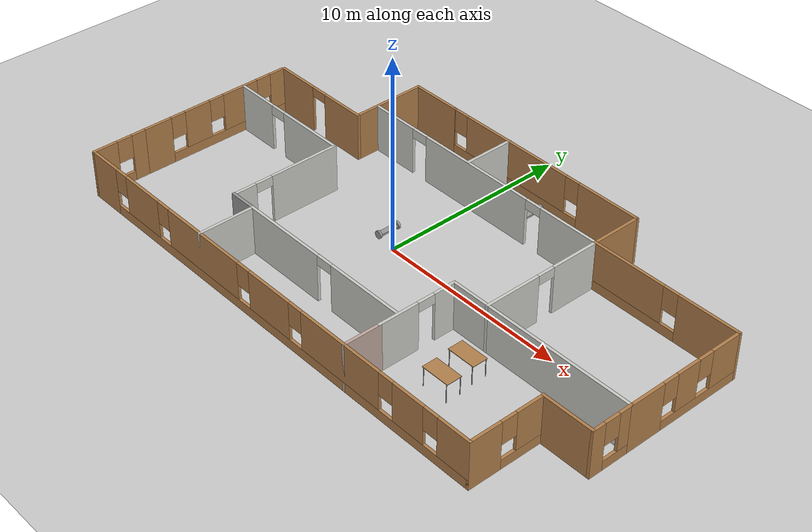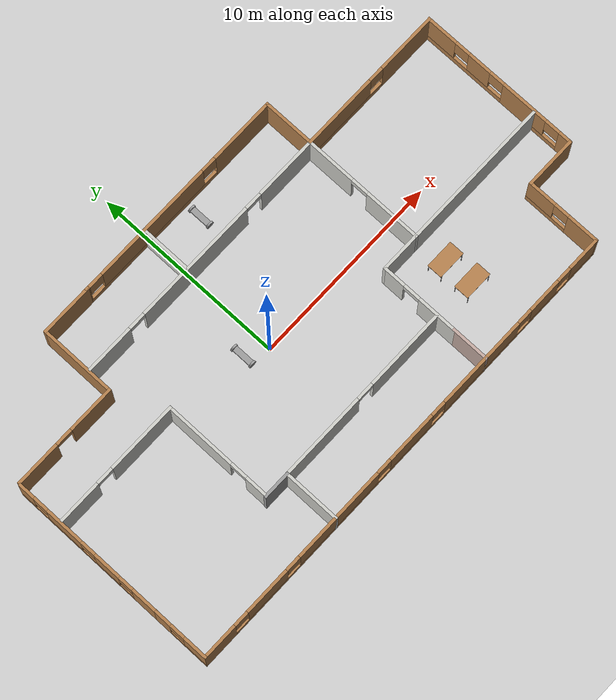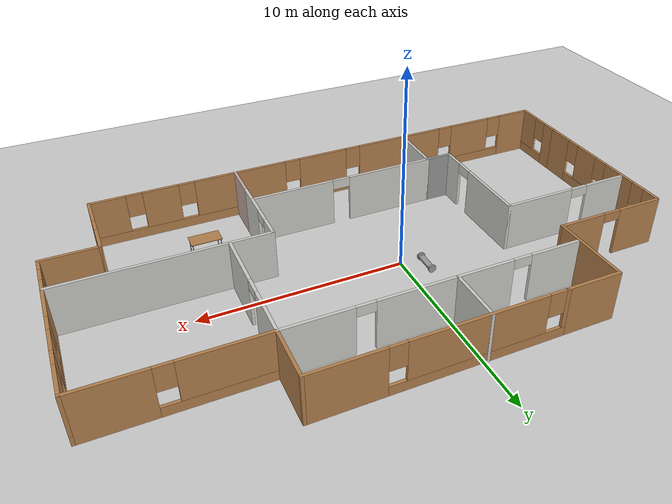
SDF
<sdf version="1.6">
 <world name="default">
  <plugin name="welcome" filename="libwelcome.so"/>
  <light name="sun" type="directional">
   <pose>0 0 10 0 -0 0</pose>
   <diffuse>0.8 0.8 0.8 1</diffuse>
   <specular>0.2 0.2 0.2 1</specular>
   <attenuation>
    <range>1000</range>
    <constant>0.9</constant>
    <linear>0.01</linear>
    <quadratic>0.001</quadratic>
   </attenuation>
   <direction>-0.5 0.1 -0.9</direction>
  </light>
  <model name="ground_plane">
   <static>1</static>
   <link name="link">
    <collision name="collision">
     <geometry><plane><normal>0 0 1</normal><size>100 100</size></plane></geometry>
     <surface>
      <contact><collide_bitmask>65535</collide_bitmask></contact>
      <friction><ode><mu>100</mu><mu2>50</mu2></ode></friction>
     </surface>
    </collision>
    <visual name="visual">
     <cast_shadows>0</cast_shadows>
     <geometry><plane><normal>0 0 1</normal><size>100 100</size></plane></geometry>
     <material>
      <script><uri>file://media/materials/scripts/gazebo.material</uri><name>Gazebo/Grey</name></script>
     </material>
    </visual>
   </link>
  </model>
  <gravity>0 0 -9.8</gravity>
  <magnetic_field>6e-06 2.3e-05 -4.2e-05</magnetic_field>
  <atmosphere type="adiabatic"/>
  <physics name="default_physics" default="0" type="ode">
   <max_step_size>0.001</max_step_size>
   <real_time_factor>1</real_time_factor>
   <real_time_update_rate>1000</real_time_update_rate>
  </physics>
  <scene><ambient>0.4 0.4 0.4 1</ambient><background>0.7 0.7 0.7 1</background><shadows>1</shadows></scene>
  <spherical_coordinates>
   <surface_model>EARTH_WGS84</surface_model>
   <latitude_deg>0</latitude_deg>
   <longitude_deg>0</longitude_deg>
   <elevation>0</elevation>
   <heading_deg>0</heading_deg>
  </spherical_coordinates>
  <model name="Building">
   <pose>1.74044 -0.12479 0 0 -0 0</pose>
   <link name="Wall_10">
    <pose>-1.3 -7.4566 0 0 -0 0</pose>
    <visual name="Wall_10_Visual_0">
     <pose>-11.6648 0 1.25 0 -0 0</pose>
     <geometry><box><size>1.92035 0.15 2.5</size></box></geometry>
     <material>
      <script><uri>file://media/materials/scripts/gazebo.material</uri><name>Gazebo/Wood</name></script>
      <ambient>1 1 1 1</ambient>
     </material>
     <meta><layer>0</layer></meta>
    </visual>
    <collision name="Wall_10_Collision_0">
     <geometry><box><size>1.92035 0.15 2.5</size></box></geometry>
     <pose>-11.6648 0 1.25 0 -0 0</pose>
    </collision>
    <visual name="Wall_10_Visual_1">
     <pose>0.960175 0 0.25 0 -0 0</pose>
     <geometry><box><size>23.3296 0.15 0.5</size></box></geometry>
     <material>
      <script><uri>file://media/materials/scripts/gazebo.material</uri><name>Gazebo/Wood</name></script>
      <ambient>1 1 1 1</ambient>
     </material>
     <meta><layer>0</layer></meta>
    </visual>
    <collision name="Wall_10_Collision_1">
     <geometry><box><size>23.3296 0.15 0.5</size></box></geometry>
     <pose>0.960175 0 0.25 0 -0 0</pose>
    </collision>
    <visual name="Wall_10_Visual_2">
     <pose>-8.67573 0 1.5 0 -0 0</pose>
     <geometry><box><size>2.45784 0.15 2</size></box></geometry>
     <material>
      <script><uri>file://media/materials/scripts/gazebo.material</uri><name>Gazebo/Wood</name></script>
      <ambient>1 1 1 1</ambient>
     </material>
     <meta><layer>0</layer></meta>
    </visual>
    <collision name="Wall_10_Collision_2">
     <geometry><box><size>2.45784 0.15 2</size></box></geometry>
     <pose>-8.67573 0 1.5 0 -0 0</pose>
    </collision>
    <visual name="Wall_10_Visual_3">
     <pose>-4.15423 0 1.5 0 -0 0</pose>
     <geometry><box><size>4.98515 0.15 2</size></box></geometry>
     <material>
      <script><uri>file://media/materials/scripts/gazebo.material</uri><name>Gazebo/Wood</name></script>
      <ambient>1 1 1 1</ambient>
     </material>
     <meta><layer>0</layer></meta>
    </visual>
    <collision name="Wall_10_Collision_3">
     <geometry><box><size>4.98515 0.15 2</size></box></geometry>
     <pose>-4.15423 0 1.5 0 -0 0</pose>
    </collision>
    <visual name="Wall_10_Visual_4">
     <pose>0.477931 0 1.5 0 -0 0</pose>
     <geometry><box><size>2.67918 0.15 2</size></box></geometry>
     <material>
      <script><uri>file://media/materials/scripts/gazebo.material</uri><name>Gazebo/Wood</name></script>
      <ambient>1 1 1 1</ambient>
     </material>
     <meta><layer>0</layer></meta>
    </visual>
    <collision name="Wall_10_Collision_4">
     <geometry><box><size>2.67918 0.15 2</size></box></geometry>
     <pose>0.477931 0 1.5 0 -0 0</pose>
    </collision>
    <visual name="Wall_10_Visual_5">
     <pose>5.02918 0 1.5 0 -0 0</pose>
     <geometry><box><size>4.82332 0.15 2</size></box></geometry>
     <material>
      <script><uri>file://media/materials/scripts/gazebo.material</uri><name>Gazebo/Wood</name></script>
      <ambient>1 1 1 1</ambient>
     </material>
     <meta><layer>0</layer></meta>
    </visual>
    <collision name="Wall_10_Collision_5">
     <geometry><box><size>4.82332 0.15 2</size></box></geometry>
     <pose>5.02918 0 1.5 0 -0 0</pose>
    </collision>
    <visual name="Wall_10_Visual_6">
     <pose>9.13542 0 1.5 0 -0 0</pose>
     <geometry><box><size>1.78916 0.15 2</size></box></geometry>
     <material>
      <script><uri>file://media/materials/scripts/gazebo.material</uri><name>Gazebo/Wood</name></script>
      <ambient>1 1 1 1</ambient>
     </material>
     <meta><layer>0</layer></meta>
    </visual>
    <collision name="Wall_10_Collision_6">
     <geometry><box><size>1.78916 0.15 2</size></box></geometry>
     <pose>9.13542 0 1.5 0 -0 0</pose>
    </collision>
    <visual name="Wall_10_Visual_7">
     <pose>11.7275 0 1.5 0 -0 0</pose>
     <geometry><box><size>1.795 0.15 2</size></box></geometry>
     <material>
      <script><uri>file://media/materials/scripts/gazebo.material</uri><name>Gazebo/Wood</name></script>
      <ambient>1 1 1 1</ambient>
     </material>
     <meta><layer>0</layer></meta>
    </visual>
    <collision name="Wall_10_Collision_7">
     <geometry><box><size>1.795 0.15 2</size></box></geometry>
     <pose>11.7275 0 1.5 0 -0 0</pose>
    </collision>
    <visual name="Wall_10_Visual_8">
     <pose>-10.3046 0 1.9 0 -0 0</pose>
     <geometry><box><size>0.8 0.15 1.2</size></box></geometry>
     <material>
      <script><uri>file://media/materials/scripts/gazebo.material</uri><name>Gazebo/Wood</name></script>
      <ambient>1 1 1 1</ambient>
     </material>
     <meta><layer>0</layer></meta>
    </visual>
    <collision name="Wall_10_Collision_8">
     <geometry><box><size>0.8 0.15 1.2</size></box></geometry>
     <pose>-10.3046 0 1.9 0 -0 0</pose>
    </collision>
    <visual name="Wall_10_Visual_9">
     <pose>-7.04681 0 1.9 0 -0 0</pose>
     <geometry><box><size>0.8 0.15 1.2</size></box></geometry>
     <material>
      <script><uri>file://media/materials/scripts/gazebo.material</uri><name>Gazebo/Wood</name></script>
      <ambient>1 1 1 1</ambient>
     </material>
     <meta><layer>0</layer></meta>
    </visual>
    <collision name="Wall_10_Collision_9">
     <geometry><box><size>0.8 0.15 1.2</size></box></geometry>
     <pose>-7.04681 0 1.9 0 -0 0</pose>
    </collision>
    <visual name="Wall_10_Visual_10">
     <pose>-1.26166 0 1.9 0 -0 0</pose>
     <geometry><box><size>0.8 0.15 1.2</size></box></geometry>
     <material>
      <script><uri>file://media/materials/scripts/gazebo.material</uri><name>Gazebo/Wood</name></script>
      <ambient>1 1 1 1</ambient>
     </material>
     <meta><layer>0</layer></meta>
    </visual>
    <collision name="Wall_10_Collision_10">
     <geometry><box><size>0.8 0.15 1.2</size></box></geometry>
     <pose>-1.26166 0 1.9 0 -0 0</pose>
    </collision>
    <visual name="Wall_10_Visual_11">
     <pose>2.21752 0 1.9 0 -0 0</pose>
     <geometry><box><size>0.8 0.15 1.2</size></box></geometry>
     <material>
      <script><uri>file://media/materials/scripts/gazebo.material</uri><name>Gazebo/Wood</name></script>
      <ambient>1 1 1 1</ambient>
     </material>
     <meta><layer>0</layer></meta>
    </visual>
    <collision name="Wall_10_Collision_11">
     <geometry><box><size>0.8 0.15 1.2</size></box></geometry>
     <pose>2.21752 0 1.9 0 -0 0</pose>
    </collision>
    <visual name="Wall_10_Visual_12">
     <pose>7.84085 0 1.9 0 -0 0</pose>
     <geometry><box><size>0.8 0.15 1.2</size></box></geometry>
     <material>
      <script><uri>file://media/materials/scripts/gazebo.material</uri><name>Gazebo/Wood</name></script>
      <ambient>1 1 1 1</ambient>
     </material>
     <meta><layer>0</layer></meta>
    </visual>
    <collision name="Wall_10_Collision_12">
     <geometry><box><size>0.8 0.15 1.2</size></box></geometry>
     <pose>7.84085 0 1.9 0 -0 0</pose>
    </collision>
    <visual name="Wall_10_Visual_13">
     <pose>10.43 0 1.9 0 -0 0</pose>
     <geometry><box><size>0.8 0.15 1.2</size></box></geometry>
     <material>
      <script><uri>file://media/materials/scripts/gazebo.material</uri><name>Gazebo/Wood</name></script>
      <ambient>1 1 1 1</ambient>
     </material>
     <meta><layer>0</layer></meta>
    </visual>
    <collision name="Wall_10_Collision_13">
     <geometry><box><size>0.8 0.15 1.2</size></box></geometry>
     <pose>10.43 0 1.9 0 -0 0</pose>
    </collision>
   </link>
   <link name="Wall_11">
    <pose>11.25 -5.5316 0 0 -0 1.5708</pose>
    <visual name="Wall_11_Visual_0">
     <pose>-1.15767 0 1.25 0 -0 0</pose>
     <geometry><box><size>1.68466 0.15 2.5</size></box></geometry>
     <material>
      <script><uri>file://media/materials/scripts/gazebo.material</uri><name>Gazebo/Wood</name></script>
      <ambient>1 1 1 1</ambient>
     </material>
     <meta><layer>0</layer></meta>
    </visual>
    <collision name="Wall_11_Collision_0">
     <geometry><box><size>1.68466 0.15 2.5</size></box></geometry>
     <pose>-1.15767 0 1.25 0 -0 0</pose>
    </collision>
    <visual name="Wall_11_Visual_1">
     <pose>0.842329 0 0.25 0 -0 0</pose>
     <geometry><box><size>2.31534 0.15 0.5</size></box></geometry>
     <material>
      <script><uri>file://media/materials/scripts/gazebo.material</uri><name>Gazebo/Wood</name></script>
      <ambient>1 1 1 1</ambient>
     </material>
     <meta><layer>0</layer></meta>
    </visual>
    <collision name="Wall_11_Collision_1">
     <geometry><box><size>2.31534 0.15 0.5</size></box></geometry>
     <pose>0.842329 0 0.25 0 -0 0</pose>
    </collision>
    <visual name="Wall_11_Visual_2">
     <pose>1.24233 0 1.5 0 -0 0</pose>
     <geometry><box><size>1.51534 0.15 2</size></box></geometry>
     <material>
      <script><uri>file://media/materials/scripts/gazebo.material</uri><name>Gazebo/Wood</name></script>
      <ambient>1 1 1 1</ambient>
     </material>
     <meta><layer>0</layer></meta>
    </visual>
    <collision name="Wall_11_Collision_2">
     <geometry><box><size>1.51534 0.15 2</size></box></geometry>
     <pose>1.24233 0 1.5 0 -0 0</pose>
    </collision>
    <visual name="Wall_11_Visual_3">
     <pose>0.084657 0 1.9 0 -0 0</pose>
     <geometry><box><size>0.8 0.15 1.2</size></box></geometry>
     <material>
      <script><uri>file://media/materials/scripts/gazebo.material</uri><name>Gazebo/Wood</name></script>
      <ambient>1 1 1 1</ambient>
     </material>
     <meta><layer>0</layer></meta>
    </visual>
    <collision name="Wall_11_Collision_3">
     <geometry><box><size>0.8 0.15 1.2</size></box></geometry>
     <pose>0.084657 0 1.9 0 -0 0</pose>
    </collision>
   </link>
   <link name="Wall_12">
    <collision name="Wall_12_Collision">
     <geometry><box><size>2.75 0.15 2.5</size></box></geometry>
     <pose>0 0 1.25 0 -0 0</pose>
    </collision>
    <visual name="Wall_12_Visual">
     <pose>0 0 1.25 0 -0 0</pose>
     <geometry><box><size>2.75 0.15 2.5</size></box></geometry>
     <material>
      <script><uri>file://media/materials/scripts/gazebo.material</uri><name>Gazebo/Wood</name></script>
      <ambient>1 1 1 1</ambient>
     </material>
     <meta><layer>0</layer></meta>
    </visual>
    <pose>12.55 -3.6066 0 0 -0 0</pose>
   </link>
   <link name="Wall_13">
    <pose>13.85 -2.5566 0 0 -0 1.5708</pose>
    <visual name="Wall_13_Visual_0">
     <pose>-0.771499 0 1.25 0 -0 0</pose>
     <geometry><box><size>0.707003 0.15 2.5</size></box></geometry>
     <material>
      <script><uri>file://media/materials/scripts/gazebo.material</uri><name>Gazebo/Wood</name></script>
      <ambient>1 1 1 1</ambient>
     </material>
     <meta><layer>0</layer></meta>
    </visual>
    <collision name="Wall_13_Collision_0">
     <geometry><box><size>0.707003 0.15 2.5</size></box></geometry>
     <pose>-0.771499 0 1.25 0 -0 0</pose>
    </collision>
    <visual name="Wall_13_Visual_1">
     <pose>0.353501 0 0.25 0 -0 0</pose>
     <geometry><box><size>1.543 0.15 0.5</size></box></geometry>
     <material>
      <script><uri>file://media/materials/scripts/gazebo.material</uri><name>Gazebo/Wood</name></script>
      <ambient>1 1 1 1</ambient>
     </material>
     <meta><layer>0</layer></meta>
    </visual>
    <collision name="Wall_13_Collision_1">
     <geometry><box><size>1.543 0.15 0.5</size></box></geometry>
     <pose>0.353501 0 0.25 0 -0 0</pose>
    </collision>
    <visual name="Wall_13_Visual_2">
     <pose>0.753501 0 1.5 0 -0 0</pose>
     <geometry><box><size>0.742997 0.15 2</size></box></geometry>
     <material>
      <script><uri>file://media/materials/scripts/gazebo.material</uri><name>Gazebo/Wood</name></script>
      <ambient>1 1 1 1</ambient>
     </material>
     <meta><layer>0</layer></meta>
    </visual>
    <collision name="Wall_13_Collision_2">
     <geometry><box><size>0.742997 0.15 2</size></box></geometry>
     <pose>0.753501 0 1.5 0 -0 0</pose>
    </collision>
    <visual name="Wall_13_Visual_3">
     <pose>-0.017997 0 1.9 0 -0 0</pose>
     <geometry><box><size>0.8 0.15 1.2</size></box></geometry>
     <material>
      <script><uri>file://media/materials/scripts/gazebo.material</uri><name>Gazebo/Wood</name></script>
      <ambient>1 1 1 1</ambient>
     </material>
     <meta><layer>0</layer></meta>
    </visual>
    <collision name="Wall_13_Collision_3">
     <geometry><box><size>0.8 0.15 1.2</size></box></geometry>
     <pose>-0.017997 0 1.9 0 -0 0</pose>
    </collision>
   </link>
   <link name="Wall_14">
    <collision name="Wall_14_Collision">
     <geometry><box><size>10 0.15 2.5</size></box></geometry>
     <pose>0 0 1.25 0 -0 0</pose>
    </collision>
    <visual name="Wall_14_Visual">
     <pose>0 0 1.25 0 -0 0</pose>
     <geometry><box><size>10 0.15 2.5</size></box></geometry>
     <material>
      <script><uri>file://media/materials/scripts/gazebo.material</uri><name>Gazebo/CeilingTiled</name></script>
      <ambient>0.760784 0.662745 0.627451 1</ambient>
     </material>
     <meta><layer>0</layer></meta>
    </visual>
    <pose>8.925 -1.5066 0 0 -0 3.14159</pose>
   </link>
   <link name="Wall_15">
    <pose>4 -3.5566 0 0 0 -1.5708</pose>
    <visual name="Wall_15_Visual_0">
     <pose>-1.51554 0 1.25 0 -0 0</pose>
     <geometry><box><size>1.21892 0.15 2.5</size></box></geometry>
     <material>
      <script><uri>file://media/materials/scripts/gazebo.material</uri><name>Gazebo/CeilingTiled</name></script>
      <ambient>0.760784 0.662745 0.627451 1</ambient>
     </material>
     <meta><layer>0</layer></meta>
    </visual>
    <collision name="Wall_15_Collision_0">
     <geometry><box><size>1.21892 0.15 2.5</size></box></geometry>
     <pose>-1.51554 0 1.25 0 -0 0</pose>
    </collision>
    <visual name="Wall_15_Visual_1">
     <pose>1.05946 0 1.25 0 -0 0</pose>
     <geometry><box><size>2.13108 0.15 2.5</size></box></geometry>
     <material>
      <script><uri>file://media/materials/scripts/gazebo.material</uri><name>Gazebo/CeilingTiled</name></script>
      <ambient>0.760784 0.662745 0.627451 1</ambient>
     </material>
     <meta><layer>0</layer></meta>
    </visual>
    <collision name="Wall_15_Collision_1">
     <geometry><box><size>2.13108 0.15 2.5</size></box></geometry>
     <pose>1.05946 0 1.25 0 -0 0</pose>
    </collision>
    <visual name="Wall_15_Visual_2">
     <pose>-0.45608 0 2.25 0 -0 0</pose>
     <geometry><box><size>0.9 0.15 0.5</size></box></geometry>
     <material>
      <script><uri>file://media/materials/scripts/gazebo.material</uri><name>Gazebo/CeilingTiled</name></script>
      <ambient>0.760784 0.662745 0.627451 1</ambient>
     </material>
     <meta><layer>0</layer></meta>
    </visual>
    <collision name="Wall_15_Collision_2">
     <geometry><box><size>0.9 0.15 0.5</size></box></geometry>
     <pose>-0.45608 0 2.25 0 -0 0</pose>
    </collision>
   </link>
   <link name="Wall_22">
    <pose>13.85 1.6684 0 0 -0 1.5708</pose>
    <visual name="Wall_22_Visual_0">
     <pose>-2.28782 0 1.25 0 -0 0</pose>
     <geometry><box><size>1.92436 0.15 2.5</size></box></geometry>
     <material>
      <script><uri>file://media/materials/scripts/gazebo.material</uri><name>Gazebo/Wood</name></script>
      <ambient>1 1 1 1</ambient>
     </material>
     <meta><layer>0</layer></meta>
    </visual>
    <collision name="Wall_22_Collision_0">
     <geometry><box><size>1.92436 0.15 2.5</size></box></geometry>
     <pose>-2.28782 0 1.25 0 -0 0</pose>
    </collision>
    <visual name="Wall_22_Visual_1">
     <pose>0.96218 0 0.25 0 -0 0</pose>
     <geometry><box><size>4.57564 0.15 0.5</size></box></geometry>
     <material>
      <script><uri>file://media/materials/scripts/gazebo.material</uri><name>Gazebo/Wood</name></script>
      <ambient>1 1 1 1</ambient>
     </material>
     <meta><layer>0</layer></meta>
    </visual>
    <collision name="Wall_22_Collision_1">
     <geometry><box><size>4.57564 0.15 0.5</size></box></geometry>
     <pose>0.96218 0 0.25 0 -0 0</pose>
    </collision>
    <visual name="Wall_22_Visual_2">
     <pose>0.105977 0 1.5 0 -0 0</pose>
     <geometry><box><size>1.26323 0.15 2</size></box></geometry>
     <material>
      <script><uri>file://media/materials/scripts/gazebo.material</uri><name>Gazebo/Wood</name></script>
      <ambient>1 1 1 1</ambient>
     </material>
     <meta><layer>0</layer></meta>
    </visual>
    <collision name="Wall_22_Collision_2">
     <geometry><box><size>1.26323 0.15 2</size></box></geometry>
     <pose>0.105977 0 1.5 0 -0 0</pose>
    </collision>
    <visual name="Wall_22_Visual_3">
     <pose>2.3938 0 1.5 0 -0 0</pose>
     <geometry><box><size>1.7124 0.15 2</size></box></geometry>
     <material>
      <script><uri>file://media/materials/scripts/gazebo.material</uri><name>Gazebo/Wood</name></script>
      <ambient>1 1 1 1</ambient>
     </material>
     <meta><layer>0</layer></meta>
    </visual>
    <collision name="Wall_22_Collision_3">
     <geometry><box><size>1.7124 0.15 2</size></box></geometry>
     <pose>2.3938 0 1.5 0 -0 0</pose>
    </collision>
    <visual name="Wall_22_Visual_4">
     <pose>-0.92564 0 1.9 0 -0 0</pose>
     <geometry><box><size>0.8 0.15 1.2</size></box></geometry>
     <material>
      <script><uri>file://media/materials/scripts/gazebo.material</uri><name>Gazebo/Wood</name></script>
      <ambient>1 1 1 1</ambient>
     </material>
     <meta><layer>0</layer></meta>
    </visual>
    <collision name="Wall_22_Collision_4">
     <geometry><box><size>0.8 0.15 1.2</size></box></geometry>
     <pose>-0.92564 0 1.9 0 -0 0</pose>
    </collision>
    <visual name="Wall_22_Visual_5">
     <pose>1.13759 0 1.9 0 -0 0</pose>
     <geometry><box><size>0.8 0.15 1.2</size></box></geometry>
     <material>
      <script><uri>file://media/materials/scripts/gazebo.material</uri><name>Gazebo/Wood</name></script>
      <ambient>1 1 1 1</ambient>
     </material>
     <meta><layer>0</layer></meta>
    </visual>
    <collision name="Wall_22_Collision_5">
     <geometry><box><size>0.8 0.15 1.2</size></box></geometry>
     <pose>1.13759 0 1.9 0 -0 0</pose>
    </collision>
   </link>
   <link name="Wall_23">
    <pose>9.925 4.8434 0 0 -0 3.14159</pose>
    <visual name="Wall_23_Visual_0">
     <pose>-2.38911 0 1.25 0 -0 0</pose>
     <geometry><box><size>3.22179 0.15 2.5</size></box></geometry>
     <material>
      <script><uri>file://media/materials/scripts/gazebo.material</uri><name>Gazebo/Wood</name></script>
      <ambient>1 1 1 1</ambient>
     </material>
     <meta><layer>0</layer></meta>
    </visual>
    <collision name="Wall_23_Collision_0">
     <geometry><box><size>3.22179 0.15 2.5</size></box></geometry>
     <pose>-2.38911 0 1.25 0 -0 0</pose>
    </collision>
    <visual name="Wall_23_Visual_1">
     <pose>1.61089 0 0.25 0 -0 0</pose>
     <geometry><box><size>4.77822 0.15 0.5</size></box></geometry>
     <material>
      <script><uri>file://media/materials/scripts/gazebo.material</uri><name>Gazebo/Wood</name></script>
      <ambient>1 1 1 1</ambient>
     </material>
     <meta><layer>0</layer></meta>
    </visual>
    <collision name="Wall_23_Collision_1">
     <geometry><box><size>4.77822 0.15 0.5</size></box></geometry>
     <pose>1.61089 0 0.25 0 -0 0</pose>
    </collision>
    <visual name="Wall_23_Visual_2">
     <pose>2.01089 0 1.5 0 -0 0</pose>
     <geometry><box><size>3.97822 0.15 2</size></box></geometry>
     <material>
      <script><uri>file://media/materials/scripts/gazebo.material</uri><name>Gazebo/Wood</name></script>
      <ambient>1 1 1 1</ambient>
     </material>
     <meta><layer>0</layer></meta>
    </visual>
    <collision name="Wall_23_Collision_2">
     <geometry><box><size>3.97822 0.15 2</size></box></geometry>
     <pose>2.01089 0 1.5 0 -0 0</pose>
    </collision>
    <visual name="Wall_23_Visual_3">
     <pose>-0.378215 0 1.9 0 -0 0</pose>
     <geometry><box><size>0.8 0.15 1.2</size></box></geometry>
     <material>
      <script><uri>file://media/materials/scripts/gazebo.material</uri><name>Gazebo/Wood</name></script>
      <ambient>1 1 1 1</ambient>
     </material>
     <meta><layer>0</layer></meta>
    </visual>
    <collision name="Wall_23_Collision_3">
     <geometry><box><size>0.8 0.15 1.2</size></box></geometry>
     <pose>-0.378215 0 1.9 0 -0 0</pose>
    </collision>
   </link>
   <link name="Wall_24">
    <pose>6 1.6684 0 0 0 -1.5708</pose>
    <visual name="Wall_24_Visual_0">
     <pose>-1.93333 0 1.25 0 -0 0</pose>
     <geometry><box><size>2.63334 0.15 2.5</size></box></geometry>
     <material>
      <script><uri>file://media/materials/scripts/gazebo.material</uri><name>Gazebo/CeilingTiled</name></script>
      <ambient>0.760784 0.662745 0.627451 1</ambient>
     </material>
     <meta><layer>0</layer></meta>
    </visual>
    <collision name="Wall_24_Collision_0">
     <geometry><box><size>2.63334 0.15 2.5</size></box></geometry>
     <pose>-1.93333 0 1.25 0 -0 0</pose>
    </collision>
    <visual name="Wall_24_Visual_1">
     <pose>1.76667 0 1.25 0 -0 0</pose>
     <geometry><box><size>2.96666 0.15 2.5</size></box></geometry>
     <material>
      <script><uri>file://media/materials/scripts/gazebo.material</uri><name>Gazebo/CeilingTiled</name></script>
      <ambient>0.760784 0.662745 0.627451 1</ambient>
     </material>
     <meta><layer>0</layer></meta>
    </visual>
    <collision name="Wall_24_Collision_1">
     <geometry><box><size>2.96666 0.15 2.5</size></box></geometry>
     <pose>1.76667 0 1.25 0 -0 0</pose>
    </collision>
    <visual name="Wall_24_Visual_2">
     <pose>-0.166661 0 2.25 0 -0 0</pose>
     <geometry><box><size>0.9 0.15 0.5</size></box></geometry>
     <material>
      <script><uri>file://media/materials/scripts/gazebo.material</uri><name>Gazebo/CeilingTiled</name></script>
      <ambient>0.760784 0.662745 0.627451 1</ambient>
     </material>
     <meta><layer>0</layer></meta>
    </visual>
    <collision name="Wall_24_Collision_2">
     <geometry><box><size>0.9 0.15 0.5</size></box></geometry>
     <pose>-0.166661 0 2.25 0 -0 0</pose>
    </collision>
   </link>
   <link name="Wall_26">
    <collision name="Wall_26_Collision">
     <geometry><box><size>2.75 0.15 2.5</size></box></geometry>
     <pose>0 0 1.25 0 -0 0</pose>
    </collision>
    <visual name="Wall_26_Visual">
     <pose>0 0 1.25 0 -0 0</pose>
     <geometry><box><size>2.75 0.15 2.5</size></box></geometry>
     <material>
      <script><uri>file://media/materials/scripts/gazebo.material</uri><name>Gazebo/Wood</name></script>
      <ambient>1 1 1 1</ambient>
     </material>
     <meta><layer>0</layer></meta>
    </visual>
    <pose>6 6.1434 0 0 -0 1.5708</pose>
   </link>
   <link name="Wall_27">
    <pose>0.2 7.4434 0 0 -0 3.14159</pose>
    <visual name="Wall_27_Visual_0">
     <pose>-4.12332 0 1.25 0 -0 0</pose>
     <geometry><box><size>3.50336 0.15 2.5</size></box></geometry>
     <material>
      <script><uri>file://media/materials/scripts/gazebo.material</uri><name>Gazebo/Wood</name></script>
      <ambient>1 1 1 1</ambient>
     </material>
     <meta><layer>0</layer></meta>
    </visual>
    <collision name="Wall_27_Collision_0">
     <geometry><box><size>3.50336 0.15 2.5</size></box></geometry>
     <pose>-4.12332 0 1.25 0 -0 0</pose>
    </collision>
    <visual name="Wall_27_Visual_1">
     <pose>1.75168 0 0.25 0 -0 0</pose>
     <geometry><box><size>8.24664 0.15 0.5</size></box></geometry>
     <material>
      <script><uri>file://media/materials/scripts/gazebo.material</uri><name>Gazebo/Wood</name></script>
      <ambient>1 1 1 1</ambient>
     </material>
     <meta><layer>0</layer></meta>
    </visual>
    <collision name="Wall_27_Collision_1">
     <geometry><box><size>8.24664 0.15 0.5</size></box></geometry>
     <pose>1.75168 0 0.25 0 -0 0</pose>
    </collision>
    <visual name="Wall_27_Visual_2">
     <pose>1.64913 0 1.5 0 -0 0</pose>
     <geometry><box><size>6.44155 0.15 2</size></box></geometry>
     <material>
      <script><uri>file://media/materials/scripts/gazebo.material</uri><name>Gazebo/Wood</name></script>
      <ambient>1 1 1 1</ambient>
     </material>
     <meta><layer>0</layer></meta>
    </visual>
    <collision name="Wall_27_Collision_2">
     <geometry><box><size>6.44155 0.15 2</size></box></geometry>
     <pose>1.64913 0 1.5 0 -0 0</pose>
    </collision>
    <visual name="Wall_27_Visual_3">
     <pose>5.77245 0 1.5 0 -0 0</pose>
     <geometry><box><size>0.205095 0.15 2</size></box></geometry>
     <material>
      <script><uri>file://media/materials/scripts/gazebo.material</uri><name>Gazebo/Wood</name></script>
      <ambient>1 1 1 1</ambient>
     </material>
     <meta><layer>0</layer></meta>
    </visual>
    <collision name="Wall_27_Collision_3">
     <geometry><box><size>0.205095 0.15 2</size></box></geometry>
     <pose>5.77245 0 1.5 0 -0 0</pose>
    </collision>
    <visual name="Wall_27_Visual_4">
     <pose>-1.97164 0 1.9 0 -0 0</pose>
     <geometry><box><size>0.8 0.15 1.2</size></box></geometry>
     <material>
      <script><uri>file://media/materials/scripts/gazebo.material</uri><name>Gazebo/Wood</name></script>
      <ambient>1 1 1 1</ambient>
     </material>
     <meta><layer>0</layer></meta>
    </visual>
    <collision name="Wall_27_Collision_4">
     <geometry><box><size>0.8 0.15 1.2</size></box></geometry>
     <pose>-1.97164 0 1.9 0 -0 0</pose>
    </collision>
    <visual name="Wall_27_Visual_5">
     <pose>5.2699 0 1.9 0 -0 0</pose>
     <geometry><box><size>0.8 0.15 1.2</size></box></geometry>
     <material>
      <script><uri>file://media/materials/scripts/gazebo.material</uri><name>Gazebo/Wood</name></script>
      <ambient>1 1 1 1</ambient>
     </material>
     <meta><layer>0</layer></meta>
    </visual>
    <collision name="Wall_27_Collision_5">
     <geometry><box><size>0.8 0.15 1.2</size></box></geometry>
     <pose>5.2699 0 1.9 0 -0 0</pose>
    </collision>
   </link>
   <link name="Wall_30">
    <collision name="Wall_30_Collision">
     <geometry><box><size>3 0.15 2.5</size></box></geometry>
     <pose>0 0 1.25 0 -0 0</pose>
    </collision>
    <visual name="Wall_30_Visual">
     <pose>0 0 1.25 0 -0 0</pose>
     <geometry><box><size>3 0.15 2.5</size></box></geometry>
     <material>
      <script><uri>file://media/materials/scripts/gazebo.material</uri><name>Gazebo/CeilingTiled</name></script>
      <ambient>0.760784 0.662745 0.627451 1</ambient>
     </material>
     <meta><layer>0</layer></meta>
    </visual>
    <pose>-5.65 -6.0316 0 0 0 -1.5708</pose>
   </link>
   <link name="Wall_32">
    <pose>-13.85 -0.556603 0 0 -0 1.5708</pose>
    <visual name="Wall_32_Visual_0">
     <pose>-3.38161 0 1.25 0 -0 0</pose>
     <geometry><box><size>1.48677 0.15 2.5</size></box></geometry>
     <material>
      <script><uri>file://media/materials/scripts/gazebo.material</uri><name>Gazebo/Wood</name></script>
      <ambient>1 1 1 1</ambient>
     </material>
     <meta><layer>0</layer></meta>
    </visual>
    <collision name="Wall_32_Collision_0">
     <geometry><box><size>1.48677 0.15 2.5</size></box></geometry>
     <pose>-3.38161 0 1.25 0 -0 0</pose>
    </collision>
    <visual name="Wall_32_Visual_1">
     <pose>0.743388 0 0.25 0 -0 0</pose>
     <geometry><box><size>6.76323 0.15 0.5</size></box></geometry>
     <material>
      <script><uri>file://media/materials/scripts/gazebo.material</uri><name>Gazebo/Wood</name></script>
      <ambient>1 1 1 1</ambient>
     </material>
     <meta><layer>0</layer></meta>
    </visual>
    <collision name="Wall_32_Collision_1">
     <geometry><box><size>6.76323 0.15 0.5</size></box></geometry>
     <pose>0.743388 0 0.25 0 -0 0</pose>
    </collision>
    <visual name="Wall_32_Visual_2">
     <pose>-1.11534 0 1.5 0 -0 0</pose>
     <geometry><box><size>1.44577 0.15 2</size></box></geometry>
     <material>
      <script><uri>file://media/materials/scripts/gazebo.material</uri><name>Gazebo/Wood</name></script>
      <ambient>1 1 1 1</ambient>
     </material>
     <meta><layer>0</layer></meta>
    </visual>
    <collision name="Wall_32_Collision_2">
     <geometry><box><size>1.44577 0.15 2</size></box></geometry>
     <pose>-1.11534 0 1.5 0 -0 0</pose>
    </collision>
    <visual name="Wall_32_Visual_3">
     <pose>1.42268 0 1.5 0 -0 0</pose>
     <geometry><box><size>2.03028 0.15 2</size></box></geometry>
     <material>
      <script><uri>file://media/materials/scripts/gazebo.material</uri><name>Gazebo/Wood</name></script>
      <ambient>1 1 1 1</ambient>
     </material>
     <meta><layer>0</layer></meta>
    </visual>
    <collision name="Wall_32_Collision_3">
     <geometry><box><size>2.03028 0.15 2</size></box></geometry>
     <pose>1.42268 0 1.5 0 -0 0</pose>
    </collision>
    <visual name="Wall_32_Visual_4">
     <pose>3.68141 0 1.5 0 -0 0</pose>
     <geometry><box><size>0.887175 0.15 2</size></box></geometry>
     <material>
      <script><uri>file://media/materials/scripts/gazebo.material</uri><name>Gazebo/Wood</name></script>
      <ambient>1 1 1 1</ambient>
     </material>
     <meta><layer>0</layer></meta>
    </visual>
    <collision name="Wall_32_Collision_4">
     <geometry><box><size>0.887175 0.15 2</size></box></geometry>
     <pose>3.68141 0 1.5 0 -0 0</pose>
    </collision>
    <visual name="Wall_32_Visual_5">
     <pose>-2.23822 0 1.9 0 -0 0</pose>
     <geometry><box><size>0.8 0.15 1.2</size></box></geometry>
     <material>
      <script><uri>file://media/materials/scripts/gazebo.material</uri><name>Gazebo/Wood</name></script>
      <ambient>1 1 1 1</ambient>
     </material>
     <meta><layer>0</layer></meta>
    </visual>
    <collision name="Wall_32_Collision_5">
     <geometry><box><size>0.8 0.15 1.2</size></box></geometry>
     <pose>-2.23822 0 1.9 0 -0 0</pose>
    </collision>
    <visual name="Wall_32_Visual_6">
     <pose>0.007543 0 1.9 0 -0 0</pose>
     <geometry><box><size>0.8 0.15 1.2</size></box></geometry>
     <material>
      <script><uri>file://media/materials/scripts/gazebo.material</uri><name>Gazebo/Wood</name></script>
      <ambient>1 1 1 1</ambient>
     </material>
     <meta><layer>0</layer></meta>
    </visual>
    <collision name="Wall_32_Collision_6">
     <geometry><box><size>0.8 0.15 1.2</size></box></geometry>
     <pose>0.007543 0 1.9 0 -0 0</pose>
    </collision>
    <visual name="Wall_32_Visual_7">
     <pose>2.83783 0 1.9 0 -0 0</pose>
     <geometry><box><size>0.8 0.15 1.2</size></box></geometry>
     <material>
      <script><uri>file://media/materials/scripts/gazebo.material</uri><name>Gazebo/Wood</name></script>
      <ambient>1 1 1 1</ambient>
     </material>
     <meta><layer>0</layer></meta>
    </visual>
    <collision name="Wall_32_Collision_7">
     <geometry><box><size>0.8 0.15 1.2</size></box></geometry>
     <pose>2.83783 0 1.9 0 -0 0</pose>
    </collision>
   </link>
   <link name="Wall_35">
    <pose>-0.85 -4.6066 0 0 -0 0</pose>
    <visual name="Wall_35_Visual_0">
     <pose>-2.57384 0 1.25 0 -0 0</pose>
     <geometry><box><size>4.60232 0.15 2.5</size></box></geometry>
     <material>
      <script><uri>file://media/materials/scripts/gazebo.material</uri><name>Gazebo/CeilingTiled</name></script>
      <ambient>0.760784 0.662745 0.627451 1</ambient>
     </material>
     <meta><layer>0</layer></meta>
    </visual>
    <collision name="Wall_35_Collision_0">
     <geometry><box><size>4.60232 0.15 2.5</size></box></geometry>
     <pose>-2.57384 0 1.25 0 -0 0</pose>
    </collision>
    <visual name="Wall_35_Visual_1">
     <pose>2.75116 0 1.25 0 -0 0</pose>
     <geometry><box><size>4.24768 0.15 2.5</size></box></geometry>
     <material>
      <script><uri>file://media/materials/scripts/gazebo.material</uri><name>Gazebo/CeilingTiled</name></script>
      <ambient>0.760784 0.662745 0.627451 1</ambient>
     </material>
     <meta><layer>0</layer></meta>
    </visual>
    <collision name="Wall_35_Collision_1">
     <geometry><box><size>4.24768 0.15 2.5</size></box></geometry>
     <pose>2.75116 0 1.25 0 -0 0</pose>
    </collision>
    <visual name="Wall_35_Visual_2">
     <pose>0.177316 0 2.25 0 -0 0</pose>
     <geometry><box><size>0.9 0.15 0.5</size></box></geometry>
     <material>
      <script><uri>file://media/materials/scripts/gazebo.material</uri><name>Gazebo/CeilingTiled</name></script>
      <ambient>0.760784 0.662745 0.627451 1</ambient>
     </material>
     <meta><layer>0</layer></meta>
    </visual>
    <collision name="Wall_35_Collision_2">
     <geometry><box><size>0.9 0.15 0.5</size></box></geometry>
     <pose>0.177316 0 2.25 0 -0 0</pose>
    </collision>
   </link>
   <link name="Wall_39">
    <collision name="Wall_39_Collision">
     <geometry><box><size>2 0.15 2.5</size></box></geometry>
     <pose>0 0 1.25 0 -0 0</pose>
    </collision>
    <visual name="Wall_39_Visual">
     <pose>0 0 1.25 0 -0 0</pose>
     <geometry><box><size>2 0.15 2.5</size></box></geometry>
     <material>
      <script><uri>file://media/materials/scripts/gazebo.material</uri><name>Gazebo/Grey</name></script>
      <ambient>0.760784 0.662745 0.627451 1</ambient>
     </material>
     <meta><layer>0</layer></meta>
    </visual>
    <pose>4 -6.5316 0 0 0 -1.5708</pose>
   </link>
   <link name="Wall_41">
    <collision name="Wall_41_Collision">
     <geometry><box><size>2.75 0.15 2.5</size></box></geometry>
     <pose>0 0 1.25 0 -0 0</pose>
    </collision>
    <visual name="Wall_41_Visual">
     <pose>0 0 1.25 0 -0 0</pose>
     <geometry><box><size>2.75 0.15 2.5</size></box></geometry>
     <material>
      <script><uri>file://media/materials/scripts/gazebo.material</uri><name>Gazebo/Wood</name></script>
      <ambient>1 1 1 1</ambient>
     </material>
     <meta><layer>0</layer></meta>
    </visual>
    <pose>-6.9 7.4434 0 0 -0 3.14159</pose>
   </link>
   <link name="Wall_42">
    <collision name="Wall_42_Collision">
     <geometry><box><size>4 0.15 2.5</size></box></geometry>
     <pose>0 0 1.25 0 -0 0</pose>
    </collision>
    <visual name="Wall_42_Visual">
     <pose>0 0 1.25 0 -0 0</pose>
     <geometry><box><size>4 0.15 2.5</size></box></geometry>
     <material>
      <script><uri>file://media/materials/scripts/gazebo.material</uri><name>Gazebo/Wood</name></script>
      <ambient>1 1 1 1</ambient>
     </material>
     <meta><layer>0</layer></meta>
    </visual>
    <pose>-8.2 5.5184 0 0 0 -1.5708</pose>
   </link>
   <link name="Wall_43">
    <pose>-11 3.5934 0 0 -0 3.14159</pose>
    <visual name="Wall_43_Visual_0">
     <pose>-1.63823 0 1.25 0 -0 0</pose>
     <geometry><box><size>2.47355 0.15 2.5</size></box></geometry>
     <material>
      <script><uri>file://media/materials/scripts/gazebo.material</uri><name>Gazebo/Wood</name></script>
      <ambient>1 1 1 1</ambient>
     </material>
     <meta><layer>0</layer></meta>
    </visual>
    <collision name="Wall_43_Collision_0">
     <geometry><box><size>2.47355 0.15 2.5</size></box></geometry>
     <pose>-1.63823 0 1.25 0 -0 0</pose>
    </collision>
    <visual name="Wall_43_Visual_1">
     <pose>1.68677 0 1.25 0 -0 0</pose>
     <geometry><box><size>2.37645 0.15 2.5</size></box></geometry>
     <material>
      <script><uri>file://media/materials/scripts/gazebo.material</uri><name>Gazebo/Wood</name></script>
      <ambient>1 1 1 1</ambient>
     </material>
     <meta><layer>0</layer></meta>
    </visual>
    <collision name="Wall_43_Collision_1">
     <geometry><box><size>2.37645 0.15 2.5</size></box></geometry>
     <pose>1.68677 0 1.25 0 -0 0</pose>
    </collision>
    <visual name="Wall_43_Visual_2">
     <pose>0.048545 0 2.25 0 -0 0</pose>
     <geometry><box><size>0.9 0.15 0.5</size></box></geometry>
     <material>
      <script><uri>file://media/materials/scripts/gazebo.material</uri><name>Gazebo/Wood</name></script>
      <ambient>1 1 1 1</ambient>
     </material>
     <meta><layer>0</layer></meta>
    </visual>
    <collision name="Wall_43_Collision_2">
     <geometry><box><size>0.9 0.15 0.5</size></box></geometry>
     <pose>0.048545 0 2.25 0 -0 0</pose>
    </collision>
   </link>
   <link name="Wall_45">
    <pose>-1.05 4.8434 0 0 -0 3.14159</pose>
    <visual name="Wall_45_Visual_0">
     <pose>-5.45901 0 1.25 0 -0 0</pose>
     <geometry><box><size>3.33199 0.15 2.5</size></box></geometry>
     <material>
      <script><uri>file://media/materials/scripts/gazebo.material</uri><name>Gazebo/CeilingTiled</name></script>
      <ambient>0.435294 0.796078 0.67451 1</ambient>
     </material>
     <meta><layer>0</layer></meta>
    </visual>
    <collision name="Wall_45_Collision_0">
     <geometry><box><size>3.33199 0.15 2.5</size></box></geometry>
     <pose>-5.45901 0 1.25 0 -0 0</pose>
    </collision>
    <visual name="Wall_45_Visual_1">
     <pose>0.378903 0 1.25 0 -0 0</pose>
     <geometry><box><size>6.54383 0.15 2.5</size></box></geometry>
     <material>
      <script><uri>file://media/materials/scripts/gazebo.material</uri><name>Gazebo/CeilingTiled</name></script>
      <ambient>0.435294 0.796078 0.67451 1</ambient>
     </material>
     <meta><layer>0</layer></meta>
    </visual>
    <collision name="Wall_45_Collision_1">
     <geometry><box><size>6.54383 0.15 2.5</size></box></geometry>
     <pose>0.378903 0 1.25 0 -0 0</pose>
    </collision>
    <visual name="Wall_45_Visual_2">
     <pose>5.83791 0 1.25 0 -0 0</pose>
     <geometry><box><size>2.57418 0.15 2.5</size></box></geometry>
     <material>
      <script><uri>file://media/materials/scripts/gazebo.material</uri><name>Gazebo/CeilingTiled</name></script>
      <ambient>0.435294 0.796078 0.67451 1</ambient>
     </material>
     <meta><layer>0</layer></meta>
    </visual>
    <collision name="Wall_45_Collision_2">
     <geometry><box><size>2.57418 0.15 2.5</size></box></geometry>
     <pose>5.83791 0 1.25 0 -0 0</pose>
    </collision>
    <visual name="Wall_45_Visual_3">
     <pose>-3.34301 0 2.25 0 -0 0</pose>
     <geometry><box><size>0.9 0.15 0.5</size></box></geometry>
     <material>
      <script><uri>file://media/materials/scripts/gazebo.material</uri><name>Gazebo/CeilingTiled</name></script>
      <ambient>0.435294 0.796078 0.67451 1</ambient>
     </material>
     <meta><layer>0</layer></meta>
    </visual>
    <collision name="Wall_45_Collision_3">
     <geometry><box><size>0.9 0.15 0.5</size></box></geometry>
     <pose>-3.34301 0 2.25 0 -0 0</pose>
    </collision>
    <visual name="Wall_45_Visual_4">
     <pose>4.10082 0 2.25 0 -0 0</pose>
     <geometry><box><size>0.9 0.15 0.5</size></box></geometry>
     <material>
      <script><uri>file://media/materials/scripts/gazebo.material</uri><name>Gazebo/CeilingTiled</name></script>
      <ambient>0.435294 0.796078 0.67451 1</ambient>
     </material>
     <meta><layer>0</layer></meta>
    </visual>
    <collision name="Wall_45_Collision_4">
     <geometry><box><size>0.9 0.15 0.5</size></box></geometry>
     <pose>4.10082 0 2.25 0 -0 0</pose>
    </collision>
   </link>
   <link name="Wall_62">
    <collision name="Wall_62_Collision">
     <geometry><box><size>2.75 0.15 2.5</size></box></geometry>
     <pose>0 0 1.25 0 -0 0</pose>
    </collision>
    <visual name="Wall_62_Visual">
     <pose>0 0 1.25 0 -0 0</pose>
     <geometry><box><size>2.75 0.15 2.5</size></box></geometry>
     <material>
      <script><uri>file://media/materials/scripts/gazebo.material</uri><name>Gazebo/CeilingTiled</name></script>
      <ambient>0.435294 0.796078 0.67451 1</ambient>
     </material>
     <meta><layer>0</layer></meta>
    </visual>
    <pose>-1.92894 6.1566 0 0 0 -1.5708</pose>
   </link>
   <link name="Wall_70">
    <pose>-10.3923 1.11219 0 0 -0 0</pose>
    <visual name="Wall_70_Visual_0">
     <pose>-2.3185 0 1.25 0 -0 0</pose>
     <geometry><box><size>2.36299 0.15 2.5</size></box></geometry>
     <material>
      <script><uri>file://media/materials/scripts/gazebo.material</uri><name>Gazebo/CeilingTiled</name></script>
      <ambient>1 1 1 1</ambient>
     </material>
     <meta><layer>0</layer></meta>
    </visual>
    <collision name="Wall_70_Collision_0">
     <geometry><box><size>2.36299 0.15 2.5</size></box></geometry>
     <pose>-2.3185 0 1.25 0 -0 0</pose>
    </collision>
    <visual name="Wall_70_Visual_1">
     <pose>1.6315 0 1.25 0 -0 0</pose>
     <geometry><box><size>3.73701 0.15 2.5</size></box></geometry>
     <material>
      <script><uri>file://media/materials/scripts/gazebo.material</uri><name>Gazebo/CeilingTiled</name></script>
      <ambient>1 1 1 1</ambient>
     </material>
     <meta><layer>0</layer></meta>
    </visual>
    <collision name="Wall_70_Collision_1">
     <geometry><box><size>3.73701 0.15 2.5</size></box></geometry>
     <pose>1.6315 0 1.25 0 -0 0</pose>
    </collision>
    <visual name="Wall_70_Visual_2">
     <pose>-0.687009 0 2.25 0 -0 0</pose>
     <geometry><box><size>0.9 0.15 0.5</size></box></geometry>
     <material>
      <script><uri>file://media/materials/scripts/gazebo.material</uri><name>Gazebo/CeilingTiled</name></script>
      <ambient>1 1 1 1</ambient>
     </material>
     <meta><layer>0</layer></meta>
    </visual>
    <collision name="Wall_70_Collision_2">
     <geometry><box><size>0.9 0.15 0.5</size></box></geometry>
     <pose>-0.687009 0 2.25 0 -0 0</pose>
    </collision>
   </link>
   <link name="Wall_71">
    <pose>-6.9673 -1.68781 0 0 0 -1.5708</pose>
    <visual name="Wall_71_Visual_0">
     <pose>-1.0167 0 1.25 0 -0 0</pose>
     <geometry><box><size>3.7166 0.15 2.5</size></box></geometry>
     <material>
      <script><uri>file://media/materials/scripts/gazebo.material</uri><name>Gazebo/CeilingTiled</name></script>
      <ambient>0.760784 0.662745 0.627451 1</ambient>
     </material>
     <meta><layer>0</layer></meta>
    </visual>
    <collision name="Wall_71_Collision_0">
     <geometry><box><size>3.7166 0.15 2.5</size></box></geometry>
     <pose>-1.0167 0 1.25 0 -0 0</pose>
    </collision>
    <visual name="Wall_71_Visual_1">
     <pose>2.3083 0 1.25 0 -0 0</pose>
     <geometry><box><size>1.1334 0.15 2.5</size></box></geometry>
     <material>
      <script><uri>file://media/materials/scripts/gazebo.material</uri><name>Gazebo/CeilingTiled</name></script>
      <ambient>0.760784 0.662745 0.627451 1</ambient>
     </material>
     <meta><layer>0</layer></meta>
    </visual>
    <collision name="Wall_71_Collision_1">
     <geometry><box><size>1.1334 0.15 2.5</size></box></geometry>
     <pose>2.3083 0 1.25 0 -0 0</pose>
    </collision>
    <visual name="Wall_71_Visual_2">
     <pose>1.2916 0 2.25 0 -0 0</pose>
     <geometry><box><size>0.9 0.15 0.5</size></box></geometry>
     <material>
      <script><uri>file://media/materials/scripts/gazebo.material</uri><name>Gazebo/CeilingTiled</name></script>
      <ambient>0.760784 0.662745 0.627451 1</ambient>
     </material>
     <meta><layer>0</layer></meta>
    </visual>
    <collision name="Wall_71_Collision_2">
     <geometry><box><size>0.9 0.15 0.5</size></box></geometry>
     <pose>1.2916 0 2.25 0 -0 0</pose>
    </collision>
   </link>
   <link name="Wall_73">
    <collision name="Wall_73_Collision">
     <geometry><box><size>1.5 0.15 2.5</size></box></geometry>
     <pose>0 0 1.25 0 -0 0</pose>
    </collision>
    <visual name="Wall_73_Visual">
     <pose>0 0 1.25 0 -0 0</pose>
     <geometry><box><size>1.5 0.15 2.5</size></box></geometry>
     <material>
      <script><uri>file://media/materials/scripts/gazebo.material</uri><name>Gazebo/Grey</name></script>
      <ambient>1 1 1 1</ambient>
     </material>
     <meta><layer>0</layer></meta>
    </visual>
    <pose>-6.325 -4.6066 0 0 -0 3.14159</pose>
   </link>
   <link name="Wall_9">
    <pose>-13.85 -6.0316 0 0 0 -1.5708</pose>
    <visual name="Wall_9_Visual_0">
     <pose>-1.04858 0 1.25 0 -0 0</pose>
     <geometry><box><size>0.90285 0.15 2.5</size></box></geometry>
     <material>
      <script><uri>file://media/materials/scripts/gazebo.material</uri><name>Gazebo/Wood</name></script>
      <ambient>1 1 1 1</ambient>
     </material>
     <meta><layer>0</layer></meta>
    </visual>
    <collision name="Wall_9_Collision_0">
     <geometry><box><size>0.90285 0.15 2.5</size></box></geometry>
     <pose>-1.04858 0 1.25 0 -0 0</pose>
    </collision>
    <visual name="Wall_9_Visual_1">
     <pose>0.451425 0 0.25 0 -0 0</pose>
     <geometry><box><size>2.09715 0.15 0.5</size></box></geometry>
     <material>
      <script><uri>file://media/materials/scripts/gazebo.material</uri><name>Gazebo/Wood</name></script>
      <ambient>1 1 1 1</ambient>
     </material>
     <meta><layer>0</layer></meta>
    </visual>
    <collision name="Wall_9_Collision_1">
     <geometry><box><size>2.09715 0.15 0.5</size></box></geometry>
     <pose>0.451425 0 0.25 0 -0 0</pose>
    </collision>
    <visual name="Wall_9_Visual_2">
     <pose>0.851425 0 1.5 0 -0 0</pose>
     <geometry><box><size>1.29715 0.15 2</size></box></geometry>
     <material>
      <script><uri>file://media/materials/scripts/gazebo.material</uri><name>Gazebo/Wood</name></script>
      <ambient>1 1 1 1</ambient>
     </material>
     <meta><layer>0</layer></meta>
    </visual>
    <collision name="Wall_9_Collision_2">
     <geometry><box><size>1.29715 0.15 2</size></box></geometry>
     <pose>0.851425 0 1.5 0 -0 0</pose>
    </collision>
    <visual name="Wall_9_Visual_3">
     <pose>-0.19715 0 1.9 0 -0 0</pose>
     <geometry><box><size>0.8 0.15 1.2</size></box></geometry>
     <material>
      <script><uri>file://media/materials/scripts/gazebo.material</uri><name>Gazebo/Wood</name></script>
      <ambient>1 1 1 1</ambient>
     </material>
     <meta><layer>0</layer></meta>
    </visual>
    <collision name="Wall_9_Collision_3">
     <geometry><box><size>0.8 0.15 1.2</size></box></geometry>
     <pose>-0.19715 0 1.9 0 -0 0</pose>
    </collision>
   </link>
   <static>1</static>
  </model>
  <model name="Robot">
   <link name="link_1">
    <pose>-1.10468 -1.28715 0.05 0 -0 0</pose>
    <inertial>
     <mass>1</mass>
     <inertia>
      <ixx>0.166667</ixx>
      <ixy>0</ixy>
      <ixz>0</ixz>
      <iyy>0.166667</iyy>
      <iyz>0</iyz>
      <izz>0.166667</izz>
     </inertia>
    </inertial>
    <visual name="visual">
     <geometry><box><size>0.3 1 0.1</size></box></geometry>
     <material>
      <lighting>1</lighting>
      <script><uri>file://media/materials/scripts/gazebo.material</uri><name>Gazebo/Grey</name></script>
      <shader type="pixel"><normal_map>__default__</normal_map></shader>
      <ambient>0.3 0.3 0.3 1</ambient>
      <diffuse>0.7 0.7 0.7 1</diffuse>
      <specular>0.01 0.01 0.01 1</specular>
      <emissive>0 0 0 1</emissive>
     </material>
    </visual>
    <collision name="collision">
     <geometry><box><size>0.3 1 0.1</size></box></geometry>
     <surface>
      <friction>
       <ode><mu>1</mu><mu2>1</mu2><fdir1>0 0 0</fdir1><slip1>0</slip1><slip2>0</slip2></ode>
       <torsional>
        <coefficient>1</coefficient>
        <patch_radius>0</patch_radius>
        <surface_radius>0</surface_radius>
        <use_patch_radius>1</use_patch_radius>
        <ode><slip>0</slip></ode>
       </torsional>
      </friction>
      <bounce><restitution_coefficient>0</restitution_coefficient><threshold>1e+06</threshold></bounce>
      <contact>
       <collide_without_contact>0</collide_without_contact>
       <collide_without_contact_bitmask>1</collide_without_contact_bitmask>
       <collide_bitmask>1</collide_bitmask>
       <ode>
        <soft_cfm>0</soft_cfm>
        <soft_erp>0.2</soft_erp>
        <kp>1e+13</kp>
        <kd>1</kd>
        <max_vel>0.01</max_vel>
        <min_depth>0</min_depth>
       </ode>
       <bullet>
        <split_impulse>1</split_impulse>
        <split_impulse_penetration_threshold>-0.01</split_impulse_penetration_threshold>
        <soft_cfm>0</soft_cfm>
        <soft_erp>0.2</soft_erp>
        <kp>1e+13</kp>
        <kd>1</kd>
       </bullet>
      </contact>
     </surface>
    </collision>
   </link>
   <link name="link_2">
    <pose>-1.10468 -1.83717 0.05 1.5707 -0 0</pose>
    <inertial>
     <mass>1</mass>
     <inertia><ixx>0.145833</ixx><ixy>0</ixy><ixz>0</ixz><iyy>0.145833</iyy><iyz>0</iyz><izz>0.125</izz></inertia>
    </inertial>
    <visual name="visual">
     <geometry><cylinder><radius>0.2</radius><length>0.1</length></cylinder></geometry>
     <material>
      <lighting>1</lighting>
      <script><uri>file://media/materials/scripts/gazebo.material</uri><name>Gazebo/Grey</name></script>
      <shader type="pixel"><normal_map>__default__</normal_map></shader>
      <ambient>0.3 0.3 0.3 1</ambient>
      <diffuse>0.7 0.7 0.7 1</diffuse>
      <specular>0.01 0.01 0.01 1</specular>
      <emissive>0 0 0 1</emissive>
     </material>
    </visual>
    <collision name="collision">
     <geometry><cylinder><radius>0.2</radius><length>0.1</length></cylinder></geometry>
     <surface>
      <friction>
       <ode><mu>1</mu><mu2>1</mu2><fdir1>0 0 0</fdir1><slip1>0</slip1><slip2>0</slip2></ode>
       <torsional>
        <coefficient>1</coefficient>
        <patch_radius>0</patch_radius>
        <surface_radius>0</surface_radius>
        <use_patch_radius>1</use_patch_radius>
        <ode><slip>0</slip></ode>
       </torsional>
      </friction>
      <bounce><restitution_coefficient>0</restitution_coefficient><threshold>1e+06</threshold></bounce>
      <contact>
       <collide_without_contact>0</collide_without_contact>
       <collide_without_contact_bitmask>1</collide_without_contact_bitmask>
       <collide_bitmask>1</collide_bitmask>
       <ode>
        <soft_cfm>0</soft_cfm>
        <soft_erp>0.2</soft_erp>
        <kp>1e+13</kp>
        <kd>1</kd>
        <max_vel>0.01</max_vel>
        <min_depth>0</min_depth>
       </ode>
       <bullet>
        <split_impulse>1</split_impulse>
        <split_impulse_penetration_threshold>-0.01</split_impulse_penetration_threshold>
        <soft_cfm>0</soft_cfm>
        <soft_erp>0.2</soft_erp>
        <kp>1e+13</kp>
        <kd>1</kd>
       </bullet>
      </contact>
     </surface>
    </collision>
   </link>
   <link name="link_2_clone">
    <pose>-1.10468 -0.737135 0.05 1.5707 -0 0</pose>
    <inertial>
     <mass>1</mass>
     <inertia><ixx>0.145833</ixx><ixy>0</ixy><ixz>0</ixz><iyy>0.145833</iyy><iyz>0</iyz><izz>0.125</izz></inertia>
    </inertial>
    <visual name="visual">
     <geometry><cylinder><radius>0.2</radius><length>0.1</length></cylinder></geometry>
     <material>
      <lighting>1</lighting>
      <script><uri>file://media/materials/scripts/gazebo.material</uri><name>Gazebo/Grey</name></script>
      <shader type="pixel"><normal_map>__default__</normal_map></shader>
      <ambient>0.3 0.3 0.3 1</ambient>
      <diffuse>0.7 0.7 0.7 1</diffuse>
      <specular>0.01 0.01 0.01 1</specular>
      <emissive>0 0 0 1</emissive>
     </material>
    </visual>
    <collision name="collision">
     <geometry><cylinder><radius>0.2</radius><length>0.1</length></cylinder></geometry>
     <surface>
      <friction>
       <ode><mu>1</mu><mu2>1</mu2><fdir1>0 0 0</fdir1><slip1>0</slip1><slip2>0</slip2></ode>
       <torsional>
        <coefficient>1</coefficient>
        <patch_radius>0</patch_radius>
        <surface_radius>0</surface_radius>
        <use_patch_radius>1</use_patch_radius>
        <ode><slip>0</slip></ode>
       </torsional>
      </friction>
      <bounce><restitution_coefficient>0</restitution_coefficient><threshold>1e+06</threshold></bounce>
      <contact>
       <collide_without_contact>0</collide_without_contact>
       <collide_without_contact_bitmask>1</collide_without_contact_bitmask>
       <collide_bitmask>1</collide_bitmask>
       <ode>
        <soft_cfm>0</soft_cfm>
        <soft_erp>0.2</soft_erp>
        <kp>1e+13</kp>
        <kd>1</kd>
        <max_vel>0.01</max_vel>
        <min_depth>0</min_depth>
       </ode>
       <bullet>
        <split_impulse>1</split_impulse>
        <split_impulse_penetration_threshold>-0.01</split_impulse_penetration_threshold>
        <soft_cfm>0</soft_cfm>
        <soft_erp>0.2</soft_erp>
        <kp>1e+13</kp>
        <kd>1</kd>
       </bullet>
      </contact>
     </surface>
    </collision>
   </link>
   <model name="Robot">
    <link name="link_1">
     <pose>-1.03845 0.629989 0.2 0 -0 0</pose>
     <inertial>
      <mass>1</mass>
      <inertia>
       <ixx>0.166667</ixx>
       <ixy>0</ixy>
       <ixz>0</ixz>
       <iyy>0.166667</iyy>
       <iyz>0</iyz>
       <izz>0.166667</izz>
      </inertia>
     </inertial>
     <visual name="visual">
      <geometry><box><size>0.3 1 0.1</size></box></geometry>
      <material>
       <lighting>1</lighting>
       <script><uri>file://media/materials/scripts/gazebo.material</uri><name>Gazebo/Grey</name></script>
       <shader type="pixel"><normal_map>__default__</normal_map></shader>
       <ambient>0.3 0.3 0.3 1</ambient>
       <diffuse>0.7 0.7 0.7 1</diffuse>
       <specular>0.01 0.01 0.01 1</specular>
       <emissive>0 0 0 1</emissive>
      </material>
     </visual>
     <collision name="collision">
      <geometry><box><size>0.3 1 0.1</size></box></geometry>
      <surface>
       <friction>
        <ode><mu>1</mu><mu2>1</mu2><fdir1>0 0 0</fdir1><slip1>0</slip1><slip2>0</slip2></ode>
        <torsional>
         <coefficient>1</coefficient>
         <patch_radius>0</patch_radius>
         <surface_radius>0</surface_radius>
         <use_patch_radius>1</use_patch_radius>
         <ode><slip>0</slip></ode>
        </torsional>
       </friction>
       <bounce><restitution_coefficient>0</restitution_coefficient><threshold>1e+06</threshold></bounce>
       <contact>
        <collide_without_contact>0</collide_without_contact>
        <collide_without_contact_bitmask>1</collide_without_contact_bitmask>
        <collide_bitmask>1</collide_bitmask>
        <ode>
         <soft_cfm>0</soft_cfm>
         <soft_erp>0.2</soft_erp>
         <kp>1e+13</kp>
         <kd>1</kd>
         <max_vel>0.01</max_vel>
         <min_depth>0</min_depth>
        </ode>
        <bullet>
         <split_impulse>1</split_impulse>
         <split_impulse_penetration_threshold>-0.01</split_impulse_penetration_threshold>
         <soft_cfm>0</soft_cfm>
         <soft_erp>0.2</soft_erp>
         <kp>1e+13</kp>
         <kd>1</kd>
        </bullet>
       </contact>
      </surface>
     </collision>
    </link>
    <link name="link_2">
     <pose>-1.03845 0.07997 0.2 1.5707 -0 0</pose>
     <inertial>
      <mass>1</mass>
      <inertia><ixx>0.145833</ixx><ixy>0</ixy><ixz>0</ixz><iyy>0.145833</iyy><iyz>0</iyz><izz>0.125</izz></inertia>
     </inertial>
     <visual name="visual">
      <geometry><cylinder><radius>0.2</radius><length>0.1</length></cylinder></geometry>
      <material>
       <lighting>1</lighting>
       <script><uri>file://media/materials/scripts/gazebo.material</uri><name>Gazebo/Grey</name></script>
       <shader type="pixel"><normal_map>__default__</normal_map></shader>
       <ambient>0.3 0.3 0.3 1</ambient>
       <diffuse>0.7 0.7 0.7 1</diffuse>
       <specular>0.01 0.01 0.01 1</specular>
       <emissive>0 0 0 1</emissive>
      </material>
     </visual>
     <collision name="collision">
      <geometry><cylinder><radius>0.2</radius><length>0.1</length></cylinder></geometry>
      <surface>
       <friction>
        <ode><mu>1</mu><mu2>1</mu2><fdir1>0 0 0</fdir1><slip1>0</slip1><slip2>0</slip2></ode>
        <torsional>
         <coefficient>1</coefficient>
         <patch_radius>0</patch_radius>
         <surface_radius>0</surface_radius>
         <use_patch_radius>1</use_patch_radius>
         <ode><slip>0</slip></ode>
        </torsional>
       </friction>
       <bounce><restitution_coefficient>0</restitution_coefficient><threshold>1e+06</threshold></bounce>
       <contact>
        <collide_without_contact>0</collide_without_contact>
        <collide_without_contact_bitmask>1</collide_without_contact_bitmask>
        <collide_bitmask>1</collide_bitmask>
        <ode>
         <soft_cfm>0</soft_cfm>
         <soft_erp>0.2</soft_erp>
         <kp>1e+13</kp>
         <kd>1</kd>
         <max_vel>0.01</max_vel>
         <min_depth>0</min_depth>
        </ode>
        <bullet>
         <split_impulse>1</split_impulse>
         <split_impulse_penetration_threshold>-0.01</split_impulse_penetration_threshold>
         <soft_cfm>0</soft_cfm>
         <soft_erp>0.2</soft_erp>
         <kp>1e+13</kp>
         <kd>1</kd>
        </bullet>
       </contact>
      </surface>
     </collision>
    </link>
    <link name="link_2_clone">
     <pose>-1.03845 1.18001 0.2 1.5707 -0 0</pose>
     <inertial>
      <mass>1</mass>
      <inertia><ixx>0.145833</ixx><ixy>0</ixy><ixz>0</ixz><iyy>0.145833</iyy><iyz>0</iyz><izz>0.125</izz></inertia>
     </inertial>
     <visual name="visual">
      <geometry><cylinder><radius>0.2</radius><length>0.1</length></cylinder></geometry>
      <material>
       <lighting>1</lighting>
       <script><uri>file://media/materials/scripts/gazebo.material</uri><name>Gazebo/Grey</name></script>
       <shader type="pixel"><normal_map>__default__</normal_map></shader>
       <ambient>0.3 0.3 0.3 1</ambient>
       <diffuse>0.7 0.7 0.7 1</diffuse>
       <specular>0.01 0.01 0.01 1</specular>
       <emissive>0 0 0 1</emissive>
      </material>
     </visual>
     <collision name="collision">
      <geometry><cylinder><radius>0.2</radius><length>0.1</length></cylinder></geometry>
      <surface>
       <friction>
        <ode><mu>1</mu><mu2>1</mu2><fdir1>0 0 0</fdir1><slip1>0</slip1><slip2>0</slip2></ode>
        <torsional>
         <coefficient>1</coefficient>
         <patch_radius>0</patch_radius>
         <surface_radius>0</surface_radius>
         <use_patch_radius>1</use_patch_radius>
         <ode><slip>0</slip></ode>
        </torsional>
       </friction>
       <bounce><restitution_coefficient>0</restitution_coefficient><threshold>1e+06</threshold></bounce>
       <contact>
        <collide_without_contact>0</collide_without_contact>
        <collide_without_contact_bitmask>1</collide_without_contact_bitmask>
        <collide_bitmask>1</collide_bitmask>
        <ode>
         <soft_cfm>0</soft_cfm>
         <soft_erp>0.2</soft_erp>
         <kp>1e+13</kp>
         <kd>1</kd>
         <max_vel>0.01</max_vel>
         <min_depth>0</min_depth>
        </ode>
        <bullet>
         <split_impulse>1</split_impulse>
         <split_impulse_penetration_threshold>-0.01</split_impulse_penetration_threshold>
         <soft_cfm>0</soft_cfm>
         <soft_erp>0.2</soft_erp>
         <kp>1e+13</kp>
         <kd>1</kd>
        </bullet>
       </contact>
      </surface>
     </collision>
    </link>
    <joint name="link_1_JOINT_0" type="revolute">
     <parent>link_1</parent>
     <child>link_2</child>
     <axis>
      <xyz>0 0 1</xyz>
      <use_parent_model_frame>0</use_parent_model_frame>
      <limit>
       <lower>-1.79769e+308</lower>
       <upper>1.79769e+308</upper>
       <effort>-1</effort>
       <velocity>-1</velocity>
      </limit>
      <dynamics>
       <spring_reference>0</spring_reference>
       <spring_stiffness>0</spring_stiffness>
       <damping>0</damping>
      </dynamics>
     </axis>
     <physics>
      <ode><limit><cfm>0</cfm><erp>0.2</erp></limit><suspension><cfm>0</cfm><erp>0.2</erp></suspension></ode>
     </physics>
    </joint>
    <joint name="link_1_JOINT_1" type="revolute">
     <parent>link_1</parent>
     <child>link_2_clone</child>
     <axis>
      <xyz>0 0 1</xyz>
      <use_parent_model_frame>0</use_parent_model_frame>
      <limit>
       <lower>-1.79769e+308</lower>
       <upper>1.79769e+308</upper>
       <effort>-1</effort>
       <velocity>-1</velocity>
      </limit>
      <dynamics>
       <spring_reference>0</spring_reference>
       <spring_stiffness>0</spring_stiffness>
       <damping>0</damping>
      </dynamics>
     </axis>
     <physics>
      <ode><limit><cfm>0</cfm><erp>0.2</erp></limit><suspension><cfm>0</cfm><erp>0.2</erp></suspension></ode>
     </physics>
    </joint>
    <static>0</static>
    <pose>3.31404 3.86145 -0.15 0 -0 0</pose>
   </model>
   <joint name="link_1_JOINT_0" type="revolute">
    <parent>link_1</parent>
    <child>link_2</child>
    <axis>
     <xyz>0 0 1</xyz>
     <use_parent_model_frame>0</use_parent_model_frame>
     <limit>
      <lower>-1.79769e+308</lower>
      <upper>1.79769e+308</upper>
      <effort>-1</effort>
      <velocity>-1</velocity>
     </limit>
     <dynamics>
      <spring_reference>0</spring_reference>
      <spring_stiffness>0</spring_stiffness>
      <damping>0</damping>
     </dynamics>
    </axis>
    <physics>
     <ode><limit><cfm>0</cfm><erp>0.2</erp></limit><suspension><cfm>0</cfm><erp>0.2</erp></suspension></ode>
    </physics>
   </joint>
   <joint name="link_1_JOINT_1" type="revolute">
    <parent>link_1</parent>
    <child>link_2_clone</child>
    <axis>
     <xyz>0 0 1</xyz>
     <use_parent_model_frame>0</use_parent_model_frame>
     <limit>
      <lower>-1.79769e+308</lower>
      <upper>1.79769e+308</upper>
      <effort>-1</effort>
      <velocity>-1</velocity>
     </limit>
     <dynamics>
      <spring_reference>0</spring_reference>
      <spring_stiffness>0</spring_stiffness>
      <damping>0</damping>
     </dynamics>
    </axis>
    <physics>
     <ode><limit><cfm>0</cfm><erp>0.2</erp></limit><suspension><cfm>0</cfm><erp>0.2</erp></suspension></ode>
    </physics>
   </joint>
   <static>0</static>
   <pose>0.066227 1.91714 0.15 0 -0 0</pose>
  </model>
  <model name="table">
   <static>1</static>
   <link name="link">
    <collision name="surface">
     <pose>0 0 1 0 -0 0</pose>
     <geometry><box><size>1.5 0.8 0.03</size></box></geometry>
     <surface><friction><ode><mu>0.6</mu><mu2>0.6</mu2></ode></friction></surface>
    </collision>
    <visual name="visual1">
     <pose>0 0 1 0 -0 0</pose>
     <geometry><box><size>1.5 0.8 0.03</size></box></geometry>
     <material>
      <script><uri>file://media/materials/scripts/gazebo.material</uri><name>Gazebo/Wood</name></script>
     </material>
    </visual>
    <collision name="front_left_leg">
     <pose>0.68 0.38 0.5 0 -0 0</pose>
     <geometry><cylinder><radius>0.02</radius><length>1</length></cylinder></geometry>
    </collision>
    <visual name="front_left_leg">
     <pose>0.68 0.38 0.5 0 -0 0</pose>
     <geometry><cylinder><radius>0.02</radius><length>1</length></cylinder></geometry>
     <material>
      <script><uri>file://media/materials/scripts/gazebo.material</uri><name>Gazebo/Grey</name></script>
     </material>
    </visual>
    <collision name="front_right_leg">
     <pose>0.68 -0.38 0.5 0 -0 0</pose>
     <geometry><cylinder><radius>0.02</radius><length>1</length></cylinder></geometry>
    </collision>
    <visual name="front_right_leg">
     <pose>0.68 -0.38 0.5 0 -0 0</pose>
     <geometry><cylinder><radius>0.02</radius><length>1</length></cylinder></geometry>
     <material>
      <script><uri>file://media/materials/scripts/gazebo.material</uri><name>Gazebo/Grey</name></script>
     </material>
    </visual>
    <collision name="back_right_leg">
     <pose>-0.68 -0.38 0.5 0 -0 0</pose>
     <geometry><cylinder><radius>0.02</radius><length>1</length></cylinder></geometry>
    </collision>
    <visual name="back_right_leg">
     <pose>-0.68 -0.38 0.5 0 -0 0</pose>
     <geometry><cylinder><radius>0.02</radius><length>1</length></cylinder></geometry>
     <material>
      <script><uri>file://media/materials/scripts/gazebo.material</uri><name>Gazebo/Grey</name></script>
     </material>
    </visual>
    <collision name="back_left_leg">
     <pose>-0.68 0.38 0.5 0 -0 0</pose>
     <geometry><cylinder><radius>0.02</radius><length>1</length></cylinder></geometry>
    </collision>
    <visual name="back_left_leg">
     <pose>-0.68 0.38 0.5 0 -0 0</pose>
     <geometry><cylinder><radius>0.02</radius><length>1</length></cylinder></geometry>
     <material>
      <script><uri>file://media/materials/scripts/gazebo.material</uri><name>Gazebo/Grey</name></script>
     </material>
    </visual>
   </link>
   <pose>8.16274 -3.10259 0 0 -0 0</pose>
  </model>
  <model name="table_0">
   <static>1</static>
   <link name="link">
    <collision name="surface">
     <pose>0 0 1 0 -0 0</pose>
     <geometry><box><size>1.5 0.8 0.03</size></box></geometry>
     <surface><friction><ode><mu>0.6</mu><mu2>0.6</mu2></ode></friction></surface>
    </collision>
    <visual name="visual1">
     <pose>0 0 1 0 -0 0</pose>
     <geometry><box><size>1.5 0.8 0.03</size></box></geometry>
     <material>
      <script><uri>file://media/materials/scripts/gazebo.material</uri><name>Gazebo/Wood</name></script>
     </material>
    </visual>
    <collision name="front_left_leg">
     <pose>0.68 0.38 0.5 0 -0 0</pose>
     <geometry><cylinder><radius>0.02</radius><length>1</length></cylinder></geometry>
    </collision>
    <visual name="front_left_leg">
     <pose>0.68 0.38 0.5 0 -0 0</pose>
     <geometry><cylinder><radius>0.02</radius><length>1</length></cylinder></geometry>
     <material>
      <script><uri>file://media/materials/scripts/gazebo.material</uri><name>Gazebo/Grey</name></script>
     </material>
    </visual>
    <collision name="front_right_leg">
     <pose>0.68 -0.38 0.5 0 -0 0</pose>
     <geometry><cylinder><radius>0.02</radius><length>1</length></cylinder></geometry>
    </collision>
    <visual name="front_right_leg">
     <pose>0.68 -0.38 0.5 0 -0 0</pose>
     <geometry><cylinder><radius>0.02</radius><length>1</length></cylinder></geometry>
     <material>
      <script><uri>file://media/materials/scripts/gazebo.material</uri><name>Gazebo/Grey</name></script>
     </material>
    </visual>
    <collision name="back_right_leg">
     <pose>-0.68 -0.38 0.5 0 -0 0</pose>
     <geometry><cylinder><radius>0.02</radius><length>1</length></cylinder></geometry>
    </collision>
    <visual name="back_right_leg">
     <pose>-0.68 -0.38 0.5 0 -0 0</pose>
     <geometry><cylinder><radius>0.02</radius><length>1</length></cylinder></geometry>
     <material>
      <script><uri>file://media/materials/scripts/gazebo.material</uri><name>Gazebo/Grey</name></script>
     </material>
    </visual>
    <collision name="back_left_leg">
     <pose>-0.68 0.38 0.5 0 -0 0</pose>
     <geometry><cylinder><radius>0.02</radius><length>1</length></cylinder></geometry>
    </collision>
    <visual name="back_left_leg">
     <pose>-0.68 0.38 0.5 0 -0 0</pose>
     <geometry><cylinder><radius>0.02</radius><length>1</length></cylinder></geometry>
     <material>
      <script><uri>file://media/materials/scripts/gazebo.material</uri><name>Gazebo/Grey</name></script>
     </material>
    </visual>
   </link>
   <pose>8.26498 -4.61463 0 0 -0 0</pose>
  </model>
 </world>
</sdf>
